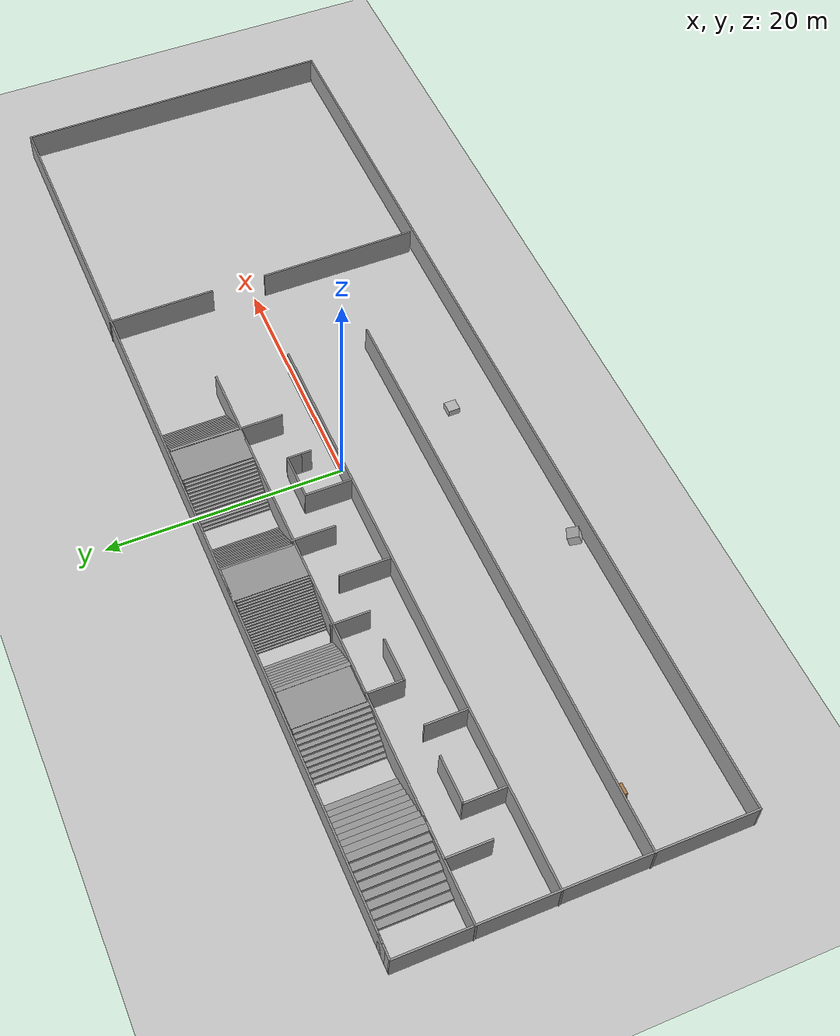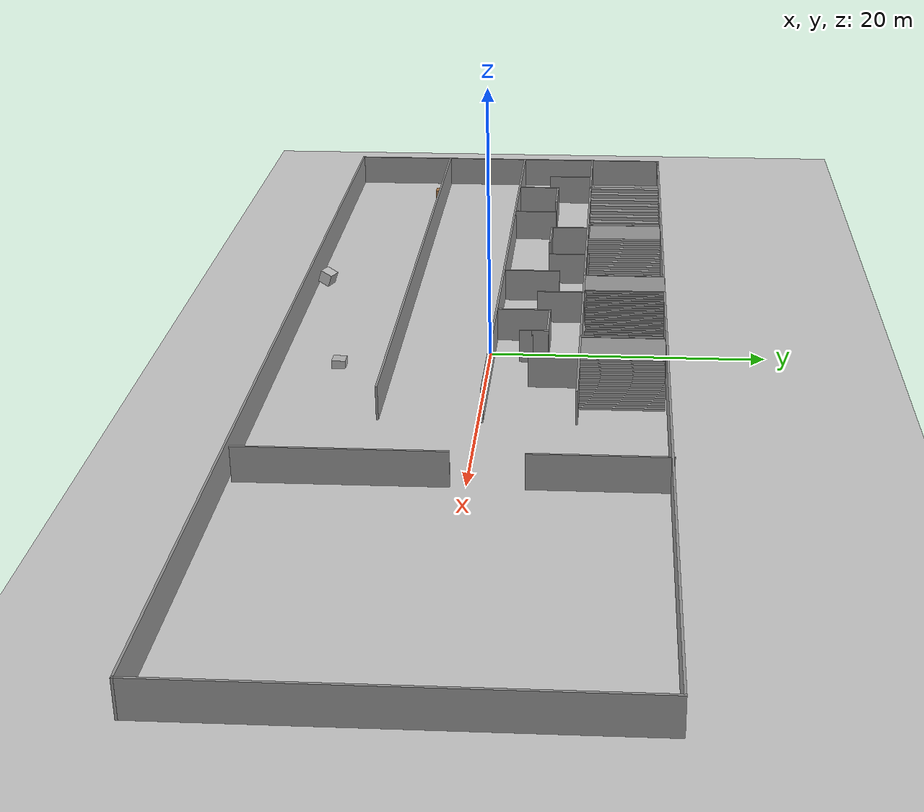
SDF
<sdf version="1.7">
 <world name="default">
  <light name="sun" type="directional">
   <pose>0 0 10 0 -0 0</pose>
   <diffuse>0.8 0.8 0.8 1</diffuse>
   <specular>0.2 0.2 0.2 1</specular>
   <attenuation>
    <range>1000</range>
    <constant>0.9</constant>
    <linear>0.01</linear>
    <quadratic>0.001</quadratic>
   </attenuation>
   <direction>-0.5 0.1 -0.9</direction>
   <spot><inner_angle>0</inner_angle><outer_angle>0</outer_angle><falloff>0</falloff></spot>
  </light>
  <model name="ground_plane">
   <static>1</static>
   <link name="link">
    <collision name="collision">
     <geometry><plane><normal>0 0 1</normal><size>100 100</size></plane></geometry>
     <surface>
      <contact><collide_bitmask>65535</collide_bitmask></contact>
      <friction><ode><mu>100</mu><mu2>50</mu2></ode></friction>
     </surface>
    </collision>
    <visual name="visual">
     <cast_shadows>0</cast_shadows>
     <geometry><plane><normal>0 0 1</normal><size>100 100</size></plane></geometry>
     <material>
      <script><uri>file://media/materials/scripts/gazebo.material</uri><name>Gazebo/Grey</name></script>
     </material>
    </visual>
   </link>
  </model>
  <gravity>0 0 -9.8</gravity>
  <magnetic_field>6e-06 2.3e-05 -4.2e-05</magnetic_field>
  <atmosphere type="adiabatic"/>
  <physics type="ode">
   <max_step_size>0.001</max_step_size>
   <real_time_factor>1</real_time_factor>
   <real_time_update_rate>1000</real_time_update_rate>
  </physics>
  <scene><ambient>0.4 0.4 0.4 1</ambient><background>0.7 0.7 0.7 1</background><shadows>1</shadows></scene>
  <audio><device>default</device></audio>
  <spherical_coordinates>
   <surface_model>EARTH_WGS84</surface_model>
   <latitude_deg>0</latitude_deg>
   <longitude_deg>0</longitude_deg>
   <elevation>0</elevation>
   <heading_deg>0</heading_deg>
  </spherical_coordinates>
  <model name="Parkour_0">
   <pose>2.61354 -1.10314 0 0 -0 0</pose>
   <link name="Stairs_0">
    <visual name="Stairs_0_Visual_0">
     <pose>6.1312 10.7342 0.083333 0 -0 -1.5708</pose>
     <geometry><box><size>5.922 0.233333 0.166667</size></box></geometry>
     <material>
      <script><uri>file://media/materials/scripts/gazebo.material</uri><name>Gazebo/Grey</name></script>
      <ambient>1 1 1 1</ambient>
     </material>
     <meta><layer>0</layer></meta>
    </visual>
    <collision name="Stairs_0_Collision_0">
     <geometry><box><size>5.922 0.233333 0.166667</size></box></geometry>
     <pose>6.1312 10.7342 0.083333 0 -0 -1.5708</pose>
    </collision>
    <visual name="Stairs_0_Visual_1">
     <pose>5.89787 10.7342 0.25 0 -0 -1.5708</pose>
     <geometry><box><size>5.922 0.233333 0.166667</size></box></geometry>
     <material>
      <script><uri>file://media/materials/scripts/gazebo.material</uri><name>Gazebo/Grey</name></script>
      <ambient>1 1 1 1</ambient>
     </material>
     <meta><layer>0</layer></meta>
    </visual>
    <collision name="Stairs_0_Collision_1">
     <geometry><box><size>5.922 0.233333 0.166667</size></box></geometry>
     <pose>5.89787 10.7342 0.25 0 -0 -1.5708</pose>
    </collision>
    <visual name="Stairs_0_Visual_2">
     <pose>5.66454 10.7342 0.416667 0 -0 -1.5708</pose>
     <geometry><box><size>5.922 0.233333 0.166667</size></box></geometry>
     <material>
      <script><uri>file://media/materials/scripts/gazebo.material</uri><name>Gazebo/Grey</name></script>
      <ambient>1 1 1 1</ambient>
     </material>
     <meta><layer>0</layer></meta>
    </visual>
    <collision name="Stairs_0_Collision_2">
     <geometry><box><size>5.922 0.233333 0.166667</size></box></geometry>
     <pose>5.66454 10.7342 0.416667 0 -0 -1.5708</pose>
    </collision>
    <visual name="Stairs_0_Visual_3">
     <pose>5.43121 10.7342 0.583333 0 -0 -1.5708</pose>
     <geometry><box><size>5.922 0.233333 0.166667</size></box></geometry>
     <material>
      <script><uri>file://media/materials/scripts/gazebo.material</uri><name>Gazebo/Grey</name></script>
      <ambient>1 1 1 1</ambient>
     </material>
     <meta><layer>0</layer></meta>
    </visual>
    <collision name="Stairs_0_Collision_3">
     <geometry><box><size>5.922 0.233333 0.166667</size></box></geometry>
     <pose>5.43121 10.7342 0.583333 0 -0 -1.5708</pose>
    </collision>
    <visual name="Stairs_0_Visual_4">
     <pose>5.19787 10.7342 0.75 0 -0 -1.5708</pose>
     <geometry><box><size>5.922 0.233333 0.166667</size></box></geometry>
     <material>
      <script><uri>file://media/materials/scripts/gazebo.material</uri><name>Gazebo/Grey</name></script>
      <ambient>1 1 1 1</ambient>
     </material>
     <meta><layer>0</layer></meta>
    </visual>
    <collision name="Stairs_0_Collision_4">
     <geometry><box><size>5.922 0.233333 0.166667</size></box></geometry>
     <pose>5.19787 10.7342 0.75 0 -0 -1.5708</pose>
    </collision>
    <visual name="Stairs_0_Visual_5">
     <pose>4.96454 10.7342 0.916667 0 -0 -1.5708</pose>
     <geometry><box><size>5.922 0.233333 0.166667</size></box></geometry>
     <material>
      <script><uri>file://media/materials/scripts/gazebo.material</uri><name>Gazebo/Grey</name></script>
      <ambient>1 1 1 1</ambient>
     </material>
     <meta><layer>0</layer></meta>
    </visual>
    <collision name="Stairs_0_Collision_5">
     <geometry><box><size>5.922 0.233333 0.166667</size></box></geometry>
     <pose>4.96454 10.7342 0.916667 0 -0 -1.5708</pose>
    </collision>
    <visual name="Stairs_0_Visual_6">
     <pose>4.73121 10.7342 1.08333 0 -0 -1.5708</pose>
     <geometry><box><size>5.922 0.233333 0.166667</size></box></geometry>
     <material>
      <script><uri>file://media/materials/scripts/gazebo.material</uri><name>Gazebo/Grey</name></script>
      <ambient>1 1 1 1</ambient>
     </material>
     <meta><layer>0</layer></meta>
    </visual>
    <collision name="Stairs_0_Collision_6">
     <geometry><box><size>5.922 0.233333 0.166667</size></box></geometry>
     <pose>4.73121 10.7342 1.08333 0 -0 -1.5708</pose>
    </collision>
    <visual name="Stairs_0_Visual_7">
     <pose>4.49787 10.7342 1.25 0 -0 -1.5708</pose>
     <geometry><box><size>5.922 0.233333 0.166667</size></box></geometry>
     <material>
      <script><uri>file://media/materials/scripts/gazebo.material</uri><name>Gazebo/Grey</name></script>
      <ambient>1 1 1 1</ambient>
     </material>
     <meta><layer>0</layer></meta>
    </visual>
    <collision name="Stairs_0_Collision_7">
     <geometry><box><size>5.922 0.233333 0.166667</size></box></geometry>
     <pose>4.49787 10.7342 1.25 0 -0 -1.5708</pose>
    </collision>
    <visual name="Stairs_0_Visual_8">
     <pose>4.26454 10.7342 1.41667 0 -0 -1.5708</pose>
     <geometry><box><size>5.922 0.233333 0.166667</size></box></geometry>
     <material>
      <script><uri>file://media/materials/scripts/gazebo.material</uri><name>Gazebo/Grey</name></script>
      <ambient>1 1 1 1</ambient>
     </material>
     <meta><layer>0</layer></meta>
    </visual>
    <collision name="Stairs_0_Collision_8">
     <geometry><box><size>5.922 0.233333 0.166667</size></box></geometry>
     <pose>4.26454 10.7342 1.41667 0 -0 -1.5708</pose>
    </collision>
    <visual name="Stairs_0_Visual_9">
     <pose>4.0312 10.7342 1.58333 0 -0 -1.5708</pose>
     <geometry><box><size>5.922 0.233333 0.166667</size></box></geometry>
     <material>
      <script><uri>file://media/materials/scripts/gazebo.material</uri><name>Gazebo/Grey</name></script>
      <ambient>1 1 1 1</ambient>
     </material>
     <meta><layer>0</layer></meta>
    </visual>
    <collision name="Stairs_0_Collision_9">
     <geometry><box><size>5.922 0.233333 0.166667</size></box></geometry>
     <pose>4.0312 10.7342 1.58333 0 -0 -1.5708</pose>
    </collision>
    <visual name="Stairs_0_Visual_10">
     <pose>3.79787 10.7342 1.75 0 -0 -1.5708</pose>
     <geometry><box><size>5.922 0.233333 0.166667</size></box></geometry>
     <material>
      <script><uri>file://media/materials/scripts/gazebo.material</uri><name>Gazebo/Grey</name></script>
      <ambient>1 1 1 1</ambient>
     </material>
     <meta><layer>0</layer></meta>
    </visual>
    <collision name="Stairs_0_Collision_10">
     <geometry><box><size>5.922 0.233333 0.166667</size></box></geometry>
     <pose>3.79787 10.7342 1.75 0 -0 -1.5708</pose>
    </collision>
    <visual name="Stairs_0_Visual_11">
     <pose>3.56454 10.7342 1.91667 0 -0 -1.5708</pose>
     <geometry><box><size>5.922 0.233333 0.166667</size></box></geometry>
     <material>
      <script><uri>file://media/materials/scripts/gazebo.material</uri><name>Gazebo/Grey</name></script>
      <ambient>1 1 1 1</ambient>
     </material>
     <meta><layer>0</layer></meta>
    </visual>
    <collision name="Stairs_0_Collision_11">
     <geometry><box><size>5.922 0.233333 0.166667</size></box></geometry>
     <pose>3.56454 10.7342 1.91667 0 -0 -1.5708</pose>
    </collision>
    <visual name="Stairs_0_Visual_12">
     <pose>3.3312 10.7342 2.08333 0 -0 -1.5708</pose>
     <geometry><box><size>5.922 0.233333 0.166667</size></box></geometry>
     <material>
      <script><uri>file://media/materials/scripts/gazebo.material</uri><name>Gazebo/Grey</name></script>
      <ambient>1 1 1 1</ambient>
     </material>
     <meta><layer>0</layer></meta>
    </visual>
    <collision name="Stairs_0_Collision_12">
     <geometry><box><size>5.922 0.233333 0.166667</size></box></geometry>
     <pose>3.3312 10.7342 2.08333 0 -0 -1.5708</pose>
    </collision>
    <visual name="Stairs_0_Visual_13">
     <pose>3.09787 10.7342 2.25 0 -0 -1.5708</pose>
     <geometry><box><size>5.922 0.233333 0.166667</size></box></geometry>
     <material>
      <script><uri>file://media/materials/scripts/gazebo.material</uri><name>Gazebo/Grey</name></script>
      <ambient>1 1 1 1</ambient>
     </material>
     <meta><layer>0</layer></meta>
    </visual>
    <collision name="Stairs_0_Collision_13">
     <geometry><box><size>5.922 0.233333 0.166667</size></box></geometry>
     <pose>3.09787 10.7342 2.25 0 -0 -1.5708</pose>
    </collision>
    <visual name="Stairs_0_Visual_14">
     <pose>2.86454 10.7342 2.41667 0 -0 -1.5708</pose>
     <geometry><box><size>5.922 0.233333 0.166667</size></box></geometry>
     <material>
      <script><uri>file://media/materials/scripts/gazebo.material</uri><name>Gazebo/Grey</name></script>
      <ambient>1 1 1 1</ambient>
     </material>
     <meta><layer>0</layer></meta>
    </visual>
    <collision name="Stairs_0_Collision_14">
     <geometry><box><size>5.922 0.233333 0.166667</size></box></geometry>
     <pose>2.86454 10.7342 2.41667 0 -0 -1.5708</pose>
    </collision>
   </link>
   <link name="Stairs_1">
    <visual name="Stairs_1_Visual_0">
     <pose>-3.78047 10.7035 0.083333 0 -0 1.5708</pose>
     <geometry><box><size>5.98376 0.233333 0.166667</size></box></geometry>
     <material>
      <script><uri>file://media/materials/scripts/gazebo.material</uri><name>Gazebo/Grey</name></script>
      <ambient>1 1 1 1</ambient>
     </material>
     <meta><layer>0</layer></meta>
    </visual>
    <collision name="Stairs_1_Collision_0">
     <geometry><box><size>5.98376 0.233333 0.166667</size></box></geometry>
     <pose>-3.78047 10.7035 0.083333 0 -0 1.5708</pose>
    </collision>
    <visual name="Stairs_1_Visual_1">
     <pose>-3.54714 10.7035 0.25 0 -0 1.5708</pose>
     <geometry><box><size>5.98376 0.233333 0.166667</size></box></geometry>
     <material>
      <script><uri>file://media/materials/scripts/gazebo.material</uri><name>Gazebo/Grey</name></script>
      <ambient>1 1 1 1</ambient>
     </material>
     <meta><layer>0</layer></meta>
    </visual>
    <collision name="Stairs_1_Collision_1">
     <geometry><box><size>5.98376 0.233333 0.166667</size></box></geometry>
     <pose>-3.54714 10.7035 0.25 0 -0 1.5708</pose>
    </collision>
    <visual name="Stairs_1_Visual_2">
     <pose>-3.31381 10.7035 0.416667 0 -0 1.5708</pose>
     <geometry><box><size>5.98376 0.233333 0.166667</size></box></geometry>
     <material>
      <script><uri>file://media/materials/scripts/gazebo.material</uri><name>Gazebo/Grey</name></script>
      <ambient>1 1 1 1</ambient>
     </material>
     <meta><layer>0</layer></meta>
    </visual>
    <collision name="Stairs_1_Collision_2">
     <geometry><box><size>5.98376 0.233333 0.166667</size></box></geometry>
     <pose>-3.31381 10.7035 0.416667 0 -0 1.5708</pose>
    </collision>
    <visual name="Stairs_1_Visual_3">
     <pose>-3.08047 10.7035 0.583333 0 -0 1.5708</pose>
     <geometry><box><size>5.98376 0.233333 0.166667</size></box></geometry>
     <material>
      <script><uri>file://media/materials/scripts/gazebo.material</uri><name>Gazebo/Grey</name></script>
      <ambient>1 1 1 1</ambient>
     </material>
     <meta><layer>0</layer></meta>
    </visual>
    <collision name="Stairs_1_Collision_3">
     <geometry><box><size>5.98376 0.233333 0.166667</size></box></geometry>
     <pose>-3.08047 10.7035 0.583333 0 -0 1.5708</pose>
    </collision>
    <visual name="Stairs_1_Visual_4">
     <pose>-2.84714 10.7035 0.75 0 -0 1.5708</pose>
     <geometry><box><size>5.98376 0.233333 0.166667</size></box></geometry>
     <material>
      <script><uri>file://media/materials/scripts/gazebo.material</uri><name>Gazebo/Grey</name></script>
      <ambient>1 1 1 1</ambient>
     </material>
     <meta><layer>0</layer></meta>
    </visual>
    <collision name="Stairs_1_Collision_4">
     <geometry><box><size>5.98376 0.233333 0.166667</size></box></geometry>
     <pose>-2.84714 10.7035 0.75 0 -0 1.5708</pose>
    </collision>
    <visual name="Stairs_1_Visual_5">
     <pose>-2.61381 10.7035 0.916667 0 -0 1.5708</pose>
     <geometry><box><size>5.98376 0.233333 0.166667</size></box></geometry>
     <material>
      <script><uri>file://media/materials/scripts/gazebo.material</uri><name>Gazebo/Grey</name></script>
      <ambient>1 1 1 1</ambient>
     </material>
     <meta><layer>0</layer></meta>
    </visual>
    <collision name="Stairs_1_Collision_5">
     <geometry><box><size>5.98376 0.233333 0.166667</size></box></geometry>
     <pose>-2.61381 10.7035 0.916667 0 -0 1.5708</pose>
    </collision>
    <visual name="Stairs_1_Visual_6">
     <pose>-2.38047 10.7035 1.08333 0 -0 1.5708</pose>
     <geometry><box><size>5.98376 0.233333 0.166667</size></box></geometry>
     <material>
      <script><uri>file://media/materials/scripts/gazebo.material</uri><name>Gazebo/Grey</name></script>
      <ambient>1 1 1 1</ambient>
     </material>
     <meta><layer>0</layer></meta>
    </visual>
    <collision name="Stairs_1_Collision_6">
     <geometry><box><size>5.98376 0.233333 0.166667</size></box></geometry>
     <pose>-2.38047 10.7035 1.08333 0 -0 1.5708</pose>
    </collision>
    <visual name="Stairs_1_Visual_7">
     <pose>-2.14714 10.7035 1.25 0 -0 1.5708</pose>
     <geometry><box><size>5.98376 0.233333 0.166667</size></box></geometry>
     <material>
      <script><uri>file://media/materials/scripts/gazebo.material</uri><name>Gazebo/Grey</name></script>
      <ambient>1 1 1 1</ambient>
     </material>
     <meta><layer>0</layer></meta>
    </visual>
    <collision name="Stairs_1_Collision_7">
     <geometry><box><size>5.98376 0.233333 0.166667</size></box></geometry>
     <pose>-2.14714 10.7035 1.25 0 -0 1.5708</pose>
    </collision>
    <visual name="Stairs_1_Visual_8">
     <pose>-1.91381 10.7035 1.41667 0 -0 1.5708</pose>
     <geometry><box><size>5.98376 0.233333 0.166667</size></box></geometry>
     <material>
      <script><uri>file://media/materials/scripts/gazebo.material</uri><name>Gazebo/Grey</name></script>
      <ambient>1 1 1 1</ambient>
     </material>
     <meta><layer>0</layer></meta>
    </visual>
    <collision name="Stairs_1_Collision_8">
     <geometry><box><size>5.98376 0.233333 0.166667</size></box></geometry>
     <pose>-1.91381 10.7035 1.41667 0 -0 1.5708</pose>
    </collision>
    <visual name="Stairs_1_Visual_9">
     <pose>-1.68047 10.7035 1.58333 0 -0 1.5708</pose>
     <geometry><box><size>5.98376 0.233333 0.166667</size></box></geometry>
     <material>
      <script><uri>file://media/materials/scripts/gazebo.material</uri><name>Gazebo/Grey</name></script>
      <ambient>1 1 1 1</ambient>
     </material>
     <meta><layer>0</layer></meta>
    </visual>
    <collision name="Stairs_1_Collision_9">
     <geometry><box><size>5.98376 0.233333 0.166667</size></box></geometry>
     <pose>-1.68047 10.7035 1.58333 0 -0 1.5708</pose>
    </collision>
    <visual name="Stairs_1_Visual_10">
     <pose>-1.44714 10.7035 1.75 0 -0 1.5708</pose>
     <geometry><box><size>5.98376 0.233333 0.166667</size></box></geometry>
     <material>
      <script><uri>file://media/materials/scripts/gazebo.material</uri><name>Gazebo/Grey</name></script>
      <ambient>1 1 1 1</ambient>
     </material>
     <meta><layer>0</layer></meta>
    </visual>
    <collision name="Stairs_1_Collision_10">
     <geometry><box><size>5.98376 0.233333 0.166667</size></box></geometry>
     <pose>-1.44714 10.7035 1.75 0 -0 1.5708</pose>
    </collision>
    <visual name="Stairs_1_Visual_11">
     <pose>-1.21381 10.7035 1.91667 0 -0 1.5708</pose>
     <geometry><box><size>5.98376 0.233333 0.166667</size></box></geometry>
     <material>
      <script><uri>file://media/materials/scripts/gazebo.material</uri><name>Gazebo/Grey</name></script>
      <ambient>1 1 1 1</ambient>
     </material>
     <meta><layer>0</layer></meta>
    </visual>
    <collision name="Stairs_1_Collision_11">
     <geometry><box><size>5.98376 0.233333 0.166667</size></box></geometry>
     <pose>-1.21381 10.7035 1.91667 0 -0 1.5708</pose>
    </collision>
    <visual name="Stairs_1_Visual_12">
     <pose>-0.980473 10.7035 2.08333 0 -0 1.5708</pose>
     <geometry><box><size>5.98376 0.233333 0.166667</size></box></geometry>
     <material>
      <script><uri>file://media/materials/scripts/gazebo.material</uri><name>Gazebo/Grey</name></script>
      <ambient>1 1 1 1</ambient>
     </material>
     <meta><layer>0</layer></meta>
    </visual>
    <collision name="Stairs_1_Collision_12">
     <geometry><box><size>5.98376 0.233333 0.166667</size></box></geometry>
     <pose>-0.980473 10.7035 2.08333 0 -0 1.5708</pose>
    </collision>
    <visual name="Stairs_1_Visual_13">
     <pose>-0.74714 10.7035 2.25 0 -0 1.5708</pose>
     <geometry><box><size>5.98376 0.233333 0.166667</size></box></geometry>
     <material>
      <script><uri>file://media/materials/scripts/gazebo.material</uri><name>Gazebo/Grey</name></script>
      <ambient>1 1 1 1</ambient>
     </material>
     <meta><layer>0</layer></meta>
    </visual>
    <collision name="Stairs_1_Collision_13">
     <geometry><box><size>5.98376 0.233333 0.166667</size></box></geometry>
     <pose>-0.74714 10.7035 2.25 0 -0 1.5708</pose>
    </collision>
    <visual name="Stairs_1_Visual_14">
     <pose>-0.513806 10.7035 2.41667 0 -0 1.5708</pose>
     <geometry><box><size>5.98376 0.233333 0.166667</size></box></geometry>
     <material>
      <script><uri>file://media/materials/scripts/gazebo.material</uri><name>Gazebo/Grey</name></script>
      <ambient>1 1 1 1</ambient>
     </material>
     <meta><layer>0</layer></meta>
    </visual>
    <collision name="Stairs_1_Collision_14">
     <geometry><box><size>5.98376 0.233333 0.166667</size></box></geometry>
     <pose>-0.513806 10.7035 2.41667 0 -0 1.5708</pose>
    </collision>
   </link>
   <link name="Stairs_2">
    <visual name="Stairs_2_Visual_0">
     <pose>-38.5274 10.758 0.15625 0 -0 1.5708</pose>
     <geometry><box><size>6.14 0.612955 0.3125</size></box></geometry>
     <material>
      <script><uri>file://media/materials/scripts/gazebo.material</uri><name>Gazebo/Grey</name></script>
      <ambient>1 1 1 1</ambient>
     </material>
     <meta><layer>0</layer></meta>
    </visual>
    <collision name="Stairs_2_Collision_0">
     <geometry><box><size>6.14 0.612955 0.3125</size></box></geometry>
     <pose>-38.5274 10.758 0.15625 0 -0 1.5708</pose>
    </collision>
    <visual name="Stairs_2_Visual_1">
     <pose>-37.9145 10.758 0.46875 0 -0 1.5708</pose>
     <geometry><box><size>6.14 0.612955 0.3125</size></box></geometry>
     <material>
      <script><uri>file://media/materials/scripts/gazebo.material</uri><name>Gazebo/Grey</name></script>
      <ambient>1 1 1 1</ambient>
     </material>
     <meta><layer>0</layer></meta>
    </visual>
    <collision name="Stairs_2_Collision_1">
     <geometry><box><size>6.14 0.612955 0.3125</size></box></geometry>
     <pose>-37.9145 10.758 0.46875 0 -0 1.5708</pose>
    </collision>
    <visual name="Stairs_2_Visual_2">
     <pose>-37.3015 10.758 0.78125 0 -0 1.5708</pose>
     <geometry><box><size>6.14 0.612955 0.3125</size></box></geometry>
     <material>
      <script><uri>file://media/materials/scripts/gazebo.material</uri><name>Gazebo/Grey</name></script>
      <ambient>1 1 1 1</ambient>
     </material>
     <meta><layer>0</layer></meta>
    </visual>
    <collision name="Stairs_2_Collision_2">
     <geometry><box><size>6.14 0.612955 0.3125</size></box></geometry>
     <pose>-37.3015 10.758 0.78125 0 -0 1.5708</pose>
    </collision>
    <visual name="Stairs_2_Visual_3">
     <pose>-36.6885 10.758 1.09375 0 -0 1.5708</pose>
     <geometry><box><size>6.14 0.612955 0.3125</size></box></geometry>
     <material>
      <script><uri>file://media/materials/scripts/gazebo.material</uri><name>Gazebo/Grey</name></script>
      <ambient>1 1 1 1</ambient>
     </material>
     <meta><layer>0</layer></meta>
    </visual>
    <collision name="Stairs_2_Collision_3">
     <geometry><box><size>6.14 0.612955 0.3125</size></box></geometry>
     <pose>-36.6885 10.758 1.09375 0 -0 1.5708</pose>
    </collision>
    <visual name="Stairs_2_Visual_4">
     <pose>-36.0756 10.758 1.40625 0 -0 1.5708</pose>
     <geometry><box><size>6.14 0.612955 0.3125</size></box></geometry>
     <material>
      <script><uri>file://media/materials/scripts/gazebo.material</uri><name>Gazebo/Grey</name></script>
      <ambient>1 1 1 1</ambient>
     </material>
     <meta><layer>0</layer></meta>
    </visual>
    <collision name="Stairs_2_Collision_4">
     <geometry><box><size>6.14 0.612955 0.3125</size></box></geometry>
     <pose>-36.0756 10.758 1.40625 0 -0 1.5708</pose>
    </collision>
    <visual name="Stairs_2_Visual_5">
     <pose>-35.4626 10.758 1.71875 0 -0 1.5708</pose>
     <geometry><box><size>6.14 0.612955 0.3125</size></box></geometry>
     <material>
      <script><uri>file://media/materials/scripts/gazebo.material</uri><name>Gazebo/Grey</name></script>
      <ambient>1 1 1 1</ambient>
     </material>
     <meta><layer>0</layer></meta>
    </visual>
    <collision name="Stairs_2_Collision_5">
     <geometry><box><size>6.14 0.612955 0.3125</size></box></geometry>
     <pose>-35.4626 10.758 1.71875 0 -0 1.5708</pose>
    </collision>
    <visual name="Stairs_2_Visual_6">
     <pose>-34.8497 10.758 2.03125 0 -0 1.5708</pose>
     <geometry><box><size>6.14 0.612955 0.3125</size></box></geometry>
     <material>
      <script><uri>file://media/materials/scripts/gazebo.material</uri><name>Gazebo/Grey</name></script>
      <ambient>1 1 1 1</ambient>
     </material>
     <meta><layer>0</layer></meta>
    </visual>
    <collision name="Stairs_2_Collision_6">
     <geometry><box><size>6.14 0.612955 0.3125</size></box></geometry>
     <pose>-34.8497 10.758 2.03125 0 -0 1.5708</pose>
    </collision>
    <visual name="Stairs_2_Visual_7">
     <pose>-34.2367 10.758 2.34375 0 -0 1.5708</pose>
     <geometry><box><size>6.14 0.612955 0.3125</size></box></geometry>
     <material>
      <script><uri>file://media/materials/scripts/gazebo.material</uri><name>Gazebo/Grey</name></script>
      <ambient>1 1 1 1</ambient>
     </material>
     <meta><layer>0</layer></meta>
    </visual>
    <collision name="Stairs_2_Collision_7">
     <geometry><box><size>6.14 0.612955 0.3125</size></box></geometry>
     <pose>-34.2367 10.758 2.34375 0 -0 1.5708</pose>
    </collision>
   </link>
   <link name="Stairs_3">
    <visual name="Stairs_3_Visual_0">
     <pose>-29.4585 10.758 0.15625 0 0 -1.5708</pose>
     <geometry><box><size>6.14 0.601258 0.3125</size></box></geometry>
     <material>
      <script><uri>file://media/materials/scripts/gazebo.material</uri><name>Gazebo/Grey</name></script>
      <ambient>1 1 1 1</ambient>
     </material>
     <meta><layer>0</layer></meta>
    </visual>
    <collision name="Stairs_3_Collision_0">
     <geometry><box><size>6.14 0.601258 0.3125</size></box></geometry>
     <pose>-29.4585 10.758 0.15625 0 0 -1.5708</pose>
    </collision>
    <visual name="Stairs_3_Visual_1">
     <pose>-30.0597 10.758 0.46875 0 0 -1.5708</pose>
     <geometry><box><size>6.14 0.601258 0.3125</size></box></geometry>
     <material>
      <script><uri>file://media/materials/scripts/gazebo.material</uri><name>Gazebo/Grey</name></script>
      <ambient>1 1 1 1</ambient>
     </material>
     <meta><layer>0</layer></meta>
    </visual>
    <collision name="Stairs_3_Collision_1">
     <geometry><box><size>6.14 0.601258 0.3125</size></box></geometry>
     <pose>-30.0597 10.758 0.46875 0 0 -1.5708</pose>
    </collision>
    <visual name="Stairs_3_Visual_2">
     <pose>-30.661 10.758 0.78125 0 0 -1.5708</pose>
     <geometry><box><size>6.14 0.601258 0.3125</size></box></geometry>
     <material>
      <script><uri>file://media/materials/scripts/gazebo.material</uri><name>Gazebo/Grey</name></script>
      <ambient>1 1 1 1</ambient>
     </material>
     <meta><layer>0</layer></meta>
    </visual>
    <collision name="Stairs_3_Collision_2">
     <geometry><box><size>6.14 0.601258 0.3125</size></box></geometry>
     <pose>-30.661 10.758 0.78125 0 0 -1.5708</pose>
    </collision>
    <visual name="Stairs_3_Visual_3">
     <pose>-31.2623 10.758 1.09375 0 0 -1.5708</pose>
     <geometry><box><size>6.14 0.601258 0.3125</size></box></geometry>
     <material>
      <script><uri>file://media/materials/scripts/gazebo.material</uri><name>Gazebo/Grey</name></script>
      <ambient>1 1 1 1</ambient>
     </material>
     <meta><layer>0</layer></meta>
    </visual>
    <collision name="Stairs_3_Collision_3">
     <geometry><box><size>6.14 0.601258 0.3125</size></box></geometry>
     <pose>-31.2623 10.758 1.09375 0 0 -1.5708</pose>
    </collision>
    <visual name="Stairs_3_Visual_4">
     <pose>-31.8635 10.758 1.40625 0 0 -1.5708</pose>
     <geometry><box><size>6.14 0.601258 0.3125</size></box></geometry>
     <material>
      <script><uri>file://media/materials/scripts/gazebo.material</uri><name>Gazebo/Grey</name></script>
      <ambient>1 1 1 1</ambient>
     </material>
     <meta><layer>0</layer></meta>
    </visual>
    <collision name="Stairs_3_Collision_4">
     <geometry><box><size>6.14 0.601258 0.3125</size></box></geometry>
     <pose>-31.8635 10.758 1.40625 0 0 -1.5708</pose>
    </collision>
    <visual name="Stairs_3_Visual_5">
     <pose>-32.4648 10.758 1.71875 0 0 -1.5708</pose>
     <geometry><box><size>6.14 0.601258 0.3125</size></box></geometry>
     <material>
      <script><uri>file://media/materials/scripts/gazebo.material</uri><name>Gazebo/Grey</name></script>
      <ambient>1 1 1 1</ambient>
     </material>
     <meta><layer>0</layer></meta>
    </visual>
    <collision name="Stairs_3_Collision_5">
     <geometry><box><size>6.14 0.601258 0.3125</size></box></geometry>
     <pose>-32.4648 10.758 1.71875 0 0 -1.5708</pose>
    </collision>
    <visual name="Stairs_3_Visual_6">
     <pose>-33.066 10.758 2.03125 0 0 -1.5708</pose>
     <geometry><box><size>6.14 0.601258 0.3125</size></box></geometry>
     <material>
      <script><uri>file://media/materials/scripts/gazebo.material</uri><name>Gazebo/Grey</name></script>
      <ambient>1 1 1 1</ambient>
     </material>
     <meta><layer>0</layer></meta>
    </visual>
    <collision name="Stairs_3_Collision_6">
     <geometry><box><size>6.14 0.601258 0.3125</size></box></geometry>
     <pose>-33.066 10.758 2.03125 0 0 -1.5708</pose>
    </collision>
    <visual name="Stairs_3_Visual_7">
     <pose>-33.6673 10.758 2.34375 0 0 -1.5708</pose>
     <geometry><box><size>6.14 0.601258 0.3125</size></box></geometry>
     <material>
      <script><uri>file://media/materials/scripts/gazebo.material</uri><name>Gazebo/Grey</name></script>
      <ambient>1 1 1 1</ambient>
     </material>
     <meta><layer>0</layer></meta>
    </visual>
    <collision name="Stairs_3_Collision_7">
     <geometry><box><size>6.14 0.601258 0.3125</size></box></geometry>
     <pose>-33.6673 10.758 2.34375 0 0 -1.5708</pose>
    </collision>
   </link>
   <link name="Stairs_4">
    <visual name="Stairs_4_Visual_0">
     <pose>1.19165 10.744 1.25 0 -0 0</pose>
     <geometry><box><size>3 6.05994 2.5</size></box></geometry>
     <material>
      <script><uri>file://media/materials/scripts/gazebo.material</uri><name>Gazebo/Grey</name></script>
      <ambient>1 1 1 1</ambient>
     </material>
     <meta><layer>0</layer></meta>
    </visual>
    <collision name="Stairs_4_Collision_0">
     <geometry><box><size>3 6.05994 2.5</size></box></geometry>
     <pose>1.19165 10.744 1.25 0 -0 0</pose>
    </collision>
   </link>
   <link name="Stairs_21">
    <visual name="Stairs_21_Visual_0">
     <pose>-10.7697 10.8664 1.25 0 -0 0</pose>
     <geometry><box><size>3 6.141 2.5</size></box></geometry>
     <material>
      <script><uri>file://media/materials/scripts/gazebo.material</uri><name>Gazebo/Grey</name></script>
      <ambient>1 1 1 1</ambient>
     </material>
     <meta><layer>0</layer></meta>
    </visual>
    <collision name="Stairs_21_Collision_0">
     <geometry><box><size>3 6.141 2.5</size></box></geometry>
     <pose>-10.7697 10.8664 1.25 0 -0 0</pose>
    </collision>
   </link>
   <link name="Stairs_22">
    <visual name="Stairs_22_Visual_0">
     <pose>-22.2123 10.8352 1.25 0 -0 0</pose>
     <geometry><box><size>3.154 5.86 2.5</size></box></geometry>
     <material>
      <script><uri>file://media/materials/scripts/gazebo.material</uri><name>Gazebo/Grey</name></script>
      <ambient>1 1 1 1</ambient>
     </material>
     <meta><layer>0</layer></meta>
    </visual>
    <collision name="Stairs_22_Collision_0">
     <geometry><box><size>3.154 5.86 2.5</size></box></geometry>
     <pose>-22.2123 10.8352 1.25 0 -0 0</pose>
    </collision>
   </link>
   <link name="Stair_fix_later">
    <visual name="Stair_fix_later_Visual_0">
     <pose>-5.89199 10.8984 0.0625 0 0 -1.5708</pose>
     <geometry><box><size>6 0.175 0.125</size></box></geometry>
     <material>
      <script><uri>file://media/materials/scripts/gazebo.material</uri><name>Gazebo/Grey</name></script>
      <ambient>1 1 1 1</ambient>
     </material>
     <meta><layer>0</layer></meta>
    </visual>
    <collision name="Stair_fix_later_Collision_0">
     <geometry><box><size>6 0.175 0.125</size></box></geometry>
     <pose>-5.89199 10.8984 0.0625 0 0 -1.5708</pose>
    </collision>
    <visual name="Stair_fix_later_Visual_1">
     <pose>-6.06699 10.8984 0.1875 0 0 -1.5708</pose>
     <geometry><box><size>6 0.175 0.125</size></box></geometry>
     <material>
      <script><uri>file://media/materials/scripts/gazebo.material</uri><name>Gazebo/Grey</name></script>
      <ambient>1 1 1 1</ambient>
     </material>
     <meta><layer>0</layer></meta>
    </visual>
    <collision name="Stair_fix_later_Collision_1">
     <geometry><box><size>6 0.175 0.125</size></box></geometry>
     <pose>-6.06699 10.8984 0.1875 0 0 -1.5708</pose>
    </collision>
    <visual name="Stair_fix_later_Visual_2">
     <pose>-6.24199 10.8984 0.3125 0 0 -1.5708</pose>
     <geometry><box><size>6 0.175 0.125</size></box></geometry>
     <material>
      <script><uri>file://media/materials/scripts/gazebo.material</uri><name>Gazebo/Grey</name></script>
      <ambient>1 1 1 1</ambient>
     </material>
     <meta><layer>0</layer></meta>
    </visual>
    <collision name="Stair_fix_later_Collision_2">
     <geometry><box><size>6 0.175 0.125</size></box></geometry>
     <pose>-6.24199 10.8984 0.3125 0 0 -1.5708</pose>
    </collision>
    <visual name="Stair_fix_later_Visual_3">
     <pose>-6.41699 10.8984 0.4375 0 0 -1.5708</pose>
     <geometry><box><size>6 0.175 0.125</size></box></geometry>
     <material>
      <script><uri>file://media/materials/scripts/gazebo.material</uri><name>Gazebo/Grey</name></script>
      <ambient>1 1 1 1</ambient>
     </material>
     <meta><layer>0</layer></meta>
    </visual>
    <collision name="Stair_fix_later_Collision_3">
     <geometry><box><size>6 0.175 0.125</size></box></geometry>
     <pose>-6.41699 10.8984 0.4375 0 0 -1.5708</pose>
    </collision>
    <visual name="Stair_fix_later_Visual_4">
     <pose>-6.59199 10.8984 0.5625 0 0 -1.5708</pose>
     <geometry><box><size>6 0.175 0.125</size></box></geometry>
     <material>
      <script><uri>file://media/materials/scripts/gazebo.material</uri><name>Gazebo/Grey</name></script>
      <ambient>1 1 1 1</ambient>
     </material>
     <meta><layer>0</layer></meta>
    </visual>
    <collision name="Stair_fix_later_Collision_4">
     <geometry><box><size>6 0.175 0.125</size></box></geometry>
     <pose>-6.59199 10.8984 0.5625 0 0 -1.5708</pose>
    </collision>
    <visual name="Stair_fix_later_Visual_5">
     <pose>-6.76699 10.8984 0.6875 0 0 -1.5708</pose>
     <geometry><box><size>6 0.175 0.125</size></box></geometry>
     <material>
      <script><uri>file://media/materials/scripts/gazebo.material</uri><name>Gazebo/Grey</name></script>
      <ambient>1 1 1 1</ambient>
     </material>
     <meta><layer>0</layer></meta>
    </visual>
    <collision name="Stair_fix_later_Collision_5">
     <geometry><box><size>6 0.175 0.125</size></box></geometry>
     <pose>-6.76699 10.8984 0.6875 0 0 -1.5708</pose>
    </collision>
    <visual name="Stair_fix_later_Visual_6">
     <pose>-6.94199 10.8984 0.8125 0 0 -1.5708</pose>
     <geometry><box><size>6 0.175 0.125</size></box></geometry>
     <material>
      <script><uri>file://media/materials/scripts/gazebo.material</uri><name>Gazebo/Grey</name></script>
      <ambient>1 1 1 1</ambient>
     </material>
     <meta><layer>0</layer></meta>
    </visual>
    <collision name="Stair_fix_later_Collision_6">
     <geometry><box><size>6 0.175 0.125</size></box></geometry>
     <pose>-6.94199 10.8984 0.8125 0 0 -1.5708</pose>
    </collision>
    <visual name="Stair_fix_later_Visual_7">
     <pose>-7.11699 10.8984 0.9375 0 0 -1.5708</pose>
     <geometry><box><size>6 0.175 0.125</size></box></geometry>
     <material>
      <script><uri>file://media/materials/scripts/gazebo.material</uri><name>Gazebo/Grey</name></script>
      <ambient>1 1 1 1</ambient>
     </material>
     <meta><layer>0</layer></meta>
    </visual>
    <collision name="Stair_fix_later_Collision_7">
     <geometry><box><size>6 0.175 0.125</size></box></geometry>
     <pose>-7.11699 10.8984 0.9375 0 0 -1.5708</pose>
    </collision>
    <visual name="Stair_fix_later_Visual_8">
     <pose>-7.29199 10.8984 1.0625 0 0 -1.5708</pose>
     <geometry><box><size>6 0.175 0.125</size></box></geometry>
     <material>
      <script><uri>file://media/materials/scripts/gazebo.material</uri><name>Gazebo/Grey</name></script>
      <ambient>1 1 1 1</ambient>
     </material>
     <meta><layer>0</layer></meta>
    </visual>
    <collision name="Stair_fix_later_Collision_8">
     <geometry><box><size>6 0.175 0.125</size></box></geometry>
     <pose>-7.29199 10.8984 1.0625 0 0 -1.5708</pose>
    </collision>
    <visual name="Stair_fix_later_Visual_9">
     <pose>-7.46699 10.8984 1.1875 0 0 -1.5708</pose>
     <geometry><box><size>6 0.175 0.125</size></box></geometry>
     <material>
      <script><uri>file://media/materials/scripts/gazebo.material</uri><name>Gazebo/Grey</name></script>
      <ambient>1 1 1 1</ambient>
     </material>
     <meta><layer>0</layer></meta>
    </visual>
    <collision name="Stair_fix_later_Collision_9">
     <geometry><box><size>6 0.175 0.125</size></box></geometry>
     <pose>-7.46699 10.8984 1.1875 0 0 -1.5708</pose>
    </collision>
    <visual name="Stair_fix_later_Visual_10">
     <pose>-7.64199 10.8984 1.3125 0 0 -1.5708</pose>
     <geometry><box><size>6 0.175 0.125</size></box></geometry>
     <material>
      <script><uri>file://media/materials/scripts/gazebo.material</uri><name>Gazebo/Grey</name></script>
      <ambient>1 1 1 1</ambient>
     </material>
     <meta><layer>0</layer></meta>
    </visual>
    <collision name="Stair_fix_later_Collision_10">
     <geometry><box><size>6 0.175 0.125</size></box></geometry>
     <pose>-7.64199 10.8984 1.3125 0 0 -1.5708</pose>
    </collision>
    <visual name="Stair_fix_later_Visual_11">
     <pose>-7.81699 10.8984 1.4375 0 0 -1.5708</pose>
     <geometry><box><size>6 0.175 0.125</size></box></geometry>
     <material>
      <script><uri>file://media/materials/scripts/gazebo.material</uri><name>Gazebo/Grey</name></script>
      <ambient>1 1 1 1</ambient>
     </material>
     <meta><layer>0</layer></meta>
    </visual>
    <collision name="Stair_fix_later_Collision_11">
     <geometry><box><size>6 0.175 0.125</size></box></geometry>
     <pose>-7.81699 10.8984 1.4375 0 0 -1.5708</pose>
    </collision>
    <visual name="Stair_fix_later_Visual_12">
     <pose>-7.99199 10.8984 1.5625 0 0 -1.5708</pose>
     <geometry><box><size>6 0.175 0.125</size></box></geometry>
     <material>
      <script><uri>file://media/materials/scripts/gazebo.material</uri><name>Gazebo/Grey</name></script>
      <ambient>1 1 1 1</ambient>
     </material>
     <meta><layer>0</layer></meta>
    </visual>
    <collision name="Stair_fix_later_Collision_12">
     <geometry><box><size>6 0.175 0.125</size></box></geometry>
     <pose>-7.99199 10.8984 1.5625 0 0 -1.5708</pose>
    </collision>
    <visual name="Stair_fix_later_Visual_13">
     <pose>-8.16699 10.8984 1.6875 0 0 -1.5708</pose>
     <geometry><box><size>6 0.175 0.125</size></box></geometry>
     <material>
      <script><uri>file://media/materials/scripts/gazebo.material</uri><name>Gazebo/Grey</name></script>
      <ambient>1 1 1 1</ambient>
     </material>
     <meta><layer>0</layer></meta>
    </visual>
    <collision name="Stair_fix_later_Collision_13">
     <geometry><box><size>6 0.175 0.125</size></box></geometry>
     <pose>-8.16699 10.8984 1.6875 0 0 -1.5708</pose>
    </collision>
    <visual name="Stair_fix_later_Visual_14">
     <pose>-8.34199 10.8984 1.8125 0 0 -1.5708</pose>
     <geometry><box><size>6 0.175 0.125</size></box></geometry>
     <material>
      <script><uri>file://media/materials/scripts/gazebo.material</uri><name>Gazebo/Grey</name></script>
      <ambient>1 1 1 1</ambient>
     </material>
     <meta><layer>0</layer></meta>
    </visual>
    <collision name="Stair_fix_later_Collision_14">
     <geometry><box><size>6 0.175 0.125</size></box></geometry>
     <pose>-8.34199 10.8984 1.8125 0 0 -1.5708</pose>
    </collision>
    <visual name="Stair_fix_later_Visual_15">
     <pose>-8.51699 10.8984 1.9375 0 0 -1.5708</pose>
     <geometry><box><size>6 0.175 0.125</size></box></geometry>
     <material>
      <script><uri>file://media/materials/scripts/gazebo.material</uri><name>Gazebo/Grey</name></script>
      <ambient>1 1 1 1</ambient>
     </material>
     <meta><layer>0</layer></meta>
    </visual>
    <collision name="Stair_fix_later_Collision_15">
     <geometry><box><size>6 0.175 0.125</size></box></geometry>
     <pose>-8.51699 10.8984 1.9375 0 0 -1.5708</pose>
    </collision>
    <visual name="Stair_fix_later_Visual_16">
     <pose>-8.69199 10.8984 2.0625 0 0 -1.5708</pose>
     <geometry><box><size>6 0.175 0.125</size></box></geometry>
     <material>
      <script><uri>file://media/materials/scripts/gazebo.material</uri><name>Gazebo/Grey</name></script>
      <ambient>1 1 1 1</ambient>
     </material>
     <meta><layer>0</layer></meta>
    </visual>
    <collision name="Stair_fix_later_Collision_16">
     <geometry><box><size>6 0.175 0.125</size></box></geometry>
     <pose>-8.69199 10.8984 2.0625 0 0 -1.5708</pose>
    </collision>
    <visual name="Stair_fix_later_Visual_17">
     <pose>-8.86699 10.8984 2.1875 0 0 -1.5708</pose>
     <geometry><box><size>6 0.175 0.125</size></box></geometry>
     <material>
      <script><uri>file://media/materials/scripts/gazebo.material</uri><name>Gazebo/Grey</name></script>
      <ambient>1 1 1 1</ambient>
     </material>
     <meta><layer>0</layer></meta>
    </visual>
    <collision name="Stair_fix_later_Collision_17">
     <geometry><box><size>6 0.175 0.125</size></box></geometry>
     <pose>-8.86699 10.8984 2.1875 0 0 -1.5708</pose>
    </collision>
    <visual name="Stair_fix_later_Visual_18">
     <pose>-9.04199 10.8984 2.3125 0 0 -1.5708</pose>
     <geometry><box><size>6 0.175 0.125</size></box></geometry>
     <material>
      <script><uri>file://media/materials/scripts/gazebo.material</uri><name>Gazebo/Grey</name></script>
      <ambient>1 1 1 1</ambient>
     </material>
     <meta><layer>0</layer></meta>
    </visual>
    <collision name="Stair_fix_later_Collision_18">
     <geometry><box><size>6 0.175 0.125</size></box></geometry>
     <pose>-9.04199 10.8984 2.3125 0 0 -1.5708</pose>
    </collision>
    <visual name="Stair_fix_later_Visual_19">
     <pose>-9.21699 10.8984 2.4375 0 0 -1.5708</pose>
     <geometry><box><size>6 0.175 0.125</size></box></geometry>
     <material>
      <script><uri>file://media/materials/scripts/gazebo.material</uri><name>Gazebo/Grey</name></script>
      <ambient>1 1 1 1</ambient>
     </material>
     <meta><layer>0</layer></meta>
    </visual>
    <collision name="Stair_fix_later_Collision_19">
     <geometry><box><size>6 0.175 0.125</size></box></geometry>
     <pose>-9.21699 10.8984 2.4375 0 0 -1.5708</pose>
    </collision>
   </link>
   <link name="Stairs_5">
    <visual name="Stairs_5_Visual_0">
     <pose>-15.7266 10.7113 0.0625 0 -0 1.5708</pose>
     <geometry><box><size>6 0.175 0.125</size></box></geometry>
     <material>
      <script><uri>file://media/materials/scripts/gazebo.material</uri><name>Gazebo/Grey</name></script>
      <ambient>1 1 1 1</ambient>
     </material>
     <meta><layer>0</layer></meta>
    </visual>
    <collision name="Stairs_5_Collision_0">
     <geometry><box><size>6 0.175 0.125</size></box></geometry>
     <pose>-15.7266 10.7113 0.0625 0 -0 1.5708</pose>
    </collision>
    <visual name="Stairs_5_Visual_1">
     <pose>-15.5516 10.7113 0.1875 0 -0 1.5708</pose>
     <geometry><box><size>6 0.175 0.125</size></box></geometry>
     <material>
      <script><uri>file://media/materials/scripts/gazebo.material</uri><name>Gazebo/Grey</name></script>
      <ambient>1 1 1 1</ambient>
     </material>
     <meta><layer>0</layer></meta>
    </visual>
    <collision name="Stairs_5_Collision_1">
     <geometry><box><size>6 0.175 0.125</size></box></geometry>
     <pose>-15.5516 10.7113 0.1875 0 -0 1.5708</pose>
    </collision>
    <visual name="Stairs_5_Visual_2">
     <pose>-15.3766 10.7113 0.3125 0 -0 1.5708</pose>
     <geometry><box><size>6 0.175 0.125</size></box></geometry>
     <material>
      <script><uri>file://media/materials/scripts/gazebo.material</uri><name>Gazebo/Grey</name></script>
      <ambient>1 1 1 1</ambient>
     </material>
     <meta><layer>0</layer></meta>
    </visual>
    <collision name="Stairs_5_Collision_2">
     <geometry><box><size>6 0.175 0.125</size></box></geometry>
     <pose>-15.3766 10.7113 0.3125 0 -0 1.5708</pose>
    </collision>
    <visual name="Stairs_5_Visual_3">
     <pose>-15.2016 10.7113 0.4375 0 -0 1.5708</pose>
     <geometry><box><size>6 0.175 0.125</size></box></geometry>
     <material>
      <script><uri>file://media/materials/scripts/gazebo.material</uri><name>Gazebo/Grey</name></script>
      <ambient>1 1 1 1</ambient>
     </material>
     <meta><layer>0</layer></meta>
    </visual>
    <collision name="Stairs_5_Collision_3">
     <geometry><box><size>6 0.175 0.125</size></box></geometry>
     <pose>-15.2016 10.7113 0.4375 0 -0 1.5708</pose>
    </collision>
    <visual name="Stairs_5_Visual_4">
     <pose>-15.0266 10.7113 0.5625 0 -0 1.5708</pose>
     <geometry><box><size>6 0.175 0.125</size></box></geometry>
     <material>
      <script><uri>file://media/materials/scripts/gazebo.material</uri><name>Gazebo/Grey</name></script>
      <ambient>1 1 1 1</ambient>
     </material>
     <meta><layer>0</layer></meta>
    </visual>
    <collision name="Stairs_5_Collision_4">
     <geometry><box><size>6 0.175 0.125</size></box></geometry>
     <pose>-15.0266 10.7113 0.5625 0 -0 1.5708</pose>
    </collision>
    <visual name="Stairs_5_Visual_5">
     <pose>-14.8516 10.7113 0.6875 0 -0 1.5708</pose>
     <geometry><box><size>6 0.175 0.125</size></box></geometry>
     <material>
      <script><uri>file://media/materials/scripts/gazebo.material</uri><name>Gazebo/Grey</name></script>
      <ambient>1 1 1 1</ambient>
     </material>
     <meta><layer>0</layer></meta>
    </visual>
    <collision name="Stairs_5_Collision_5">
     <geometry><box><size>6 0.175 0.125</size></box></geometry>
     <pose>-14.8516 10.7113 0.6875 0 -0 1.5708</pose>
    </collision>
    <visual name="Stairs_5_Visual_6">
     <pose>-14.6766 10.7113 0.8125 0 -0 1.5708</pose>
     <geometry><box><size>6 0.175 0.125</size></box></geometry>
     <material>
      <script><uri>file://media/materials/scripts/gazebo.material</uri><name>Gazebo/Grey</name></script>
      <ambient>1 1 1 1</ambient>
     </material>
     <meta><layer>0</layer></meta>
    </visual>
    <collision name="Stairs_5_Collision_6">
     <geometry><box><size>6 0.175 0.125</size></box></geometry>
     <pose>-14.6766 10.7113 0.8125 0 -0 1.5708</pose>
    </collision>
    <visual name="Stairs_5_Visual_7">
     <pose>-14.5016 10.7113 0.9375 0 -0 1.5708</pose>
     <geometry><box><size>6 0.175 0.125</size></box></geometry>
     <material>
      <script><uri>file://media/materials/scripts/gazebo.material</uri><name>Gazebo/Grey</name></script>
      <ambient>1 1 1 1</ambient>
     </material>
     <meta><layer>0</layer></meta>
    </visual>
    <collision name="Stairs_5_Collision_7">
     <geometry><box><size>6 0.175 0.125</size></box></geometry>
     <pose>-14.5016 10.7113 0.9375 0 -0 1.5708</pose>
    </collision>
    <visual name="Stairs_5_Visual_8">
     <pose>-14.3266 10.7113 1.0625 0 -0 1.5708</pose>
     <geometry><box><size>6 0.175 0.125</size></box></geometry>
     <material>
      <script><uri>file://media/materials/scripts/gazebo.material</uri><name>Gazebo/Grey</name></script>
      <ambient>1 1 1 1</ambient>
     </material>
     <meta><layer>0</layer></meta>
    </visual>
    <collision name="Stairs_5_Collision_8">
     <geometry><box><size>6 0.175 0.125</size></box></geometry>
     <pose>-14.3266 10.7113 1.0625 0 -0 1.5708</pose>
    </collision>
    <visual name="Stairs_5_Visual_9">
     <pose>-14.1516 10.7113 1.1875 0 -0 1.5708</pose>
     <geometry><box><size>6 0.175 0.125</size></box></geometry>
     <material>
      <script><uri>file://media/materials/scripts/gazebo.material</uri><name>Gazebo/Grey</name></script>
      <ambient>1 1 1 1</ambient>
     </material>
     <meta><layer>0</layer></meta>
    </visual>
    <collision name="Stairs_5_Collision_9">
     <geometry><box><size>6 0.175 0.125</size></box></geometry>
     <pose>-14.1516 10.7113 1.1875 0 -0 1.5708</pose>
    </collision>
    <visual name="Stairs_5_Visual_10">
     <pose>-13.9766 10.7113 1.3125 0 -0 1.5708</pose>
     <geometry><box><size>6 0.175 0.125</size></box></geometry>
     <material>
      <script><uri>file://media/materials/scripts/gazebo.material</uri><name>Gazebo/Grey</name></script>
      <ambient>1 1 1 1</ambient>
     </material>
     <meta><layer>0</layer></meta>
    </visual>
    <collision name="Stairs_5_Collision_10">
     <geometry><box><size>6 0.175 0.125</size></box></geometry>
     <pose>-13.9766 10.7113 1.3125 0 -0 1.5708</pose>
    </collision>
    <visual name="Stairs_5_Visual_11">
     <pose>-13.8016 10.7113 1.4375 0 -0 1.5708</pose>
     <geometry><box><size>6 0.175 0.125</size></box></geometry>
     <material>
      <script><uri>file://media/materials/scripts/gazebo.material</uri><name>Gazebo/Grey</name></script>
      <ambient>1 1 1 1</ambient>
     </material>
     <meta><layer>0</layer></meta>
    </visual>
    <collision name="Stairs_5_Collision_11">
     <geometry><box><size>6 0.175 0.125</size></box></geometry>
     <pose>-13.8016 10.7113 1.4375 0 -0 1.5708</pose>
    </collision>
    <visual name="Stairs_5_Visual_12">
     <pose>-13.6266 10.7113 1.5625 0 -0 1.5708</pose>
     <geometry><box><size>6 0.175 0.125</size></box></geometry>
     <material>
      <script><uri>file://media/materials/scripts/gazebo.material</uri><name>Gazebo/Grey</name></script>
      <ambient>1 1 1 1</ambient>
     </material>
     <meta><layer>0</layer></meta>
    </visual>
    <collision name="Stairs_5_Collision_12">
     <geometry><box><size>6 0.175 0.125</size></box></geometry>
     <pose>-13.6266 10.7113 1.5625 0 -0 1.5708</pose>
    </collision>
    <visual name="Stairs_5_Visual_13">
     <pose>-13.4516 10.7113 1.6875 0 -0 1.5708</pose>
     <geometry><box><size>6 0.175 0.125</size></box></geometry>
     <material>
      <script><uri>file://media/materials/scripts/gazebo.material</uri><name>Gazebo/Grey</name></script>
      <ambient>1 1 1 1</ambient>
     </material>
     <meta><layer>0</layer></meta>
    </visual>
    <collision name="Stairs_5_Collision_13">
     <geometry><box><size>6 0.175 0.125</size></box></geometry>
     <pose>-13.4516 10.7113 1.6875 0 -0 1.5708</pose>
    </collision>
    <visual name="Stairs_5_Visual_14">
     <pose>-13.2766 10.7113 1.8125 0 -0 1.5708</pose>
     <geometry><box><size>6 0.175 0.125</size></box></geometry>
     <material>
      <script><uri>file://media/materials/scripts/gazebo.material</uri><name>Gazebo/Grey</name></script>
      <ambient>1 1 1 1</ambient>
     </material>
     <meta><layer>0</layer></meta>
    </visual>
    <collision name="Stairs_5_Collision_14">
     <geometry><box><size>6 0.175 0.125</size></box></geometry>
     <pose>-13.2766 10.7113 1.8125 0 -0 1.5708</pose>
    </collision>
    <visual name="Stairs_5_Visual_15">
     <pose>-13.1016 10.7113 1.9375 0 -0 1.5708</pose>
     <geometry><box><size>6 0.175 0.125</size></box></geometry>
     <material>
      <script><uri>file://media/materials/scripts/gazebo.material</uri><name>Gazebo/Grey</name></script>
      <ambient>1 1 1 1</ambient>
     </material>
     <meta><layer>0</layer></meta>
    </visual>
    <collision name="Stairs_5_Collision_15">
     <geometry><box><size>6 0.175 0.125</size></box></geometry>
     <pose>-13.1016 10.7113 1.9375 0 -0 1.5708</pose>
    </collision>
    <visual name="Stairs_5_Visual_16">
     <pose>-12.9266 10.7113 2.0625 0 -0 1.5708</pose>
     <geometry><box><size>6 0.175 0.125</size></box></geometry>
     <material>
      <script><uri>file://media/materials/scripts/gazebo.material</uri><name>Gazebo/Grey</name></script>
      <ambient>1 1 1 1</ambient>
     </material>
     <meta><layer>0</layer></meta>
    </visual>
    <collision name="Stairs_5_Collision_16">
     <geometry><box><size>6 0.175 0.125</size></box></geometry>
     <pose>-12.9266 10.7113 2.0625 0 -0 1.5708</pose>
    </collision>
    <visual name="Stairs_5_Visual_17">
     <pose>-12.7516 10.7113 2.1875 0 -0 1.5708</pose>
     <geometry><box><size>6 0.175 0.125</size></box></geometry>
     <material>
      <script><uri>file://media/materials/scripts/gazebo.material</uri><name>Gazebo/Grey</name></script>
      <ambient>1 1 1 1</ambient>
     </material>
     <meta><layer>0</layer></meta>
    </visual>
    <collision name="Stairs_5_Collision_17">
     <geometry><box><size>6 0.175 0.125</size></box></geometry>
     <pose>-12.7516 10.7113 2.1875 0 -0 1.5708</pose>
    </collision>
    <visual name="Stairs_5_Visual_18">
     <pose>-12.5766 10.7113 2.3125 0 -0 1.5708</pose>
     <geometry><box><size>6 0.175 0.125</size></box></geometry>
     <material>
      <script><uri>file://media/materials/scripts/gazebo.material</uri><name>Gazebo/Grey</name></script>
      <ambient>1 1 1 1</ambient>
     </material>
     <meta><layer>0</layer></meta>
    </visual>
    <collision name="Stairs_5_Collision_18">
     <geometry><box><size>6 0.175 0.125</size></box></geometry>
     <pose>-12.5766 10.7113 2.3125 0 -0 1.5708</pose>
    </collision>
    <visual name="Stairs_5_Visual_19">
     <pose>-12.4016 10.7113 2.4375 0 -0 1.5708</pose>
     <geometry><box><size>6 0.175 0.125</size></box></geometry>
     <material>
      <script><uri>file://media/materials/scripts/gazebo.material</uri><name>Gazebo/Grey</name></script>
      <ambient>1 1 1 1</ambient>
     </material>
     <meta><layer>0</layer></meta>
    </visual>
    <collision name="Stairs_5_Collision_19">
     <geometry><box><size>6 0.175 0.125</size></box></geometry>
     <pose>-12.4016 10.7113 2.4375 0 -0 1.5708</pose>
    </collision>
   </link>
   <link name="Stairs_7">
    <visual name="Stairs_7_Visual_0">
     <pose>-17.3013 10.7628 0.125 0 0 -1.5708</pose>
     <geometry><box><size>6 0.35 0.25</size></box></geometry>
     <material>
      <script><uri>file://media/materials/scripts/gazebo.material</uri><name>Gazebo/Grey</name></script>
      <ambient>1 1 1 1</ambient>
     </material>
     <meta><layer>0</layer></meta>
    </visual>
    <collision name="Stairs_7_Collision_0">
     <geometry><box><size>6 0.35 0.25</size></box></geometry>
     <pose>-17.3013 10.7628 0.125 0 0 -1.5708</pose>
    </collision>
    <visual name="Stairs_7_Visual_1">
     <pose>-17.6513 10.7628 0.375 0 0 -1.5708</pose>
     <geometry><box><size>6 0.35 0.25</size></box></geometry>
     <material>
      <script><uri>file://media/materials/scripts/gazebo.material</uri><name>Gazebo/Grey</name></script>
      <ambient>1 1 1 1</ambient>
     </material>
     <meta><layer>0</layer></meta>
    </visual>
    <collision name="Stairs_7_Collision_1">
     <geometry><box><size>6 0.35 0.25</size></box></geometry>
     <pose>-17.6513 10.7628 0.375 0 0 -1.5708</pose>
    </collision>
    <visual name="Stairs_7_Visual_2">
     <pose>-18.0013 10.7628 0.625 0 0 -1.5708</pose>
     <geometry><box><size>6 0.35 0.25</size></box></geometry>
     <material>
      <script><uri>file://media/materials/scripts/gazebo.material</uri><name>Gazebo/Grey</name></script>
      <ambient>1 1 1 1</ambient>
     </material>
     <meta><layer>0</layer></meta>
    </visual>
    <collision name="Stairs_7_Collision_2">
     <geometry><box><size>6 0.35 0.25</size></box></geometry>
     <pose>-18.0013 10.7628 0.625 0 0 -1.5708</pose>
    </collision>
    <visual name="Stairs_7_Visual_3">
     <pose>-18.3513 10.7628 0.875 0 0 -1.5708</pose>
     <geometry><box><size>6 0.35 0.25</size></box></geometry>
     <material>
      <script><uri>file://media/materials/scripts/gazebo.material</uri><name>Gazebo/Grey</name></script>
      <ambient>1 1 1 1</ambient>
     </material>
     <meta><layer>0</layer></meta>
    </visual>
    <collision name="Stairs_7_Collision_3">
     <geometry><box><size>6 0.35 0.25</size></box></geometry>
     <pose>-18.3513 10.7628 0.875 0 0 -1.5708</pose>
    </collision>
    <visual name="Stairs_7_Visual_4">
     <pose>-18.7013 10.7628 1.125 0 0 -1.5708</pose>
     <geometry><box><size>6 0.35 0.25</size></box></geometry>
     <material>
      <script><uri>file://media/materials/scripts/gazebo.material</uri><name>Gazebo/Grey</name></script>
      <ambient>1 1 1 1</ambient>
     </material>
     <meta><layer>0</layer></meta>
    </visual>
    <collision name="Stairs_7_Collision_4">
     <geometry><box><size>6 0.35 0.25</size></box></geometry>
     <pose>-18.7013 10.7628 1.125 0 0 -1.5708</pose>
    </collision>
    <visual name="Stairs_7_Visual_5">
     <pose>-19.0513 10.7628 1.375 0 0 -1.5708</pose>
     <geometry><box><size>6 0.35 0.25</size></box></geometry>
     <material>
      <script><uri>file://media/materials/scripts/gazebo.material</uri><name>Gazebo/Grey</name></script>
      <ambient>1 1 1 1</ambient>
     </material>
     <meta><layer>0</layer></meta>
    </visual>
    <collision name="Stairs_7_Collision_5">
     <geometry><box><size>6 0.35 0.25</size></box></geometry>
     <pose>-19.0513 10.7628 1.375 0 0 -1.5708</pose>
    </collision>
    <visual name="Stairs_7_Visual_6">
     <pose>-19.4013 10.7628 1.625 0 0 -1.5708</pose>
     <geometry><box><size>6 0.35 0.25</size></box></geometry>
     <material>
      <script><uri>file://media/materials/scripts/gazebo.material</uri><name>Gazebo/Grey</name></script>
      <ambient>1 1 1 1</ambient>
     </material>
     <meta><layer>0</layer></meta>
    </visual>
    <collision name="Stairs_7_Collision_6">
     <geometry><box><size>6 0.35 0.25</size></box></geometry>
     <pose>-19.4013 10.7628 1.625 0 0 -1.5708</pose>
    </collision>
    <visual name="Stairs_7_Visual_7">
     <pose>-19.7513 10.7628 1.875 0 0 -1.5708</pose>
     <geometry><box><size>6 0.35 0.25</size></box></geometry>
     <material>
      <script><uri>file://media/materials/scripts/gazebo.material</uri><name>Gazebo/Grey</name></script>
      <ambient>1 1 1 1</ambient>
     </material>
     <meta><layer>0</layer></meta>
    </visual>
    <collision name="Stairs_7_Collision_7">
     <geometry><box><size>6 0.35 0.25</size></box></geometry>
     <pose>-19.7513 10.7628 1.875 0 0 -1.5708</pose>
    </collision>
    <visual name="Stairs_7_Visual_8">
     <pose>-20.1013 10.7628 2.125 0 0 -1.5708</pose>
     <geometry><box><size>6 0.35 0.25</size></box></geometry>
     <material>
      <script><uri>file://media/materials/scripts/gazebo.material</uri><name>Gazebo/Grey</name></script>
      <ambient>1 1 1 1</ambient>
     </material>
     <meta><layer>0</layer></meta>
    </visual>
    <collision name="Stairs_7_Collision_8">
     <geometry><box><size>6 0.35 0.25</size></box></geometry>
     <pose>-20.1013 10.7628 2.125 0 0 -1.5708</pose>
    </collision>
    <visual name="Stairs_7_Visual_9">
     <pose>-20.4513 10.7628 2.375 0 0 -1.5708</pose>
     <geometry><box><size>6 0.35 0.25</size></box></geometry>
     <material>
      <script><uri>file://media/materials/scripts/gazebo.material</uri><name>Gazebo/Grey</name></script>
      <ambient>1 1 1 1</ambient>
     </material>
     <meta><layer>0</layer></meta>
    </visual>
    <collision name="Stairs_7_Collision_9">
     <geometry><box><size>6 0.35 0.25</size></box></geometry>
     <pose>-20.4513 10.7628 2.375 0 0 -1.5708</pose>
    </collision>
   </link>
   <link name="Stairs_9">
    <visual name="Stairs_9_Visual_0">
     <pose>-27.149 10.758 0.125 0 -0 1.5708</pose>
     <geometry><box><size>5.96 0.35 0.25</size></box></geometry>
     <material>
      <script><uri>file://media/materials/scripts/gazebo.material</uri><name>Gazebo/Grey</name></script>
      <ambient>1 1 1 1</ambient>
     </material>
     <meta><layer>0</layer></meta>
    </visual>
    <collision name="Stairs_9_Collision_0">
     <geometry><box><size>5.96 0.35 0.25</size></box></geometry>
     <pose>-27.149 10.758 0.125 0 -0 1.5708</pose>
    </collision>
    <visual name="Stairs_9_Visual_1">
     <pose>-26.799 10.758 0.375 0 -0 1.5708</pose>
     <geometry><box><size>5.96 0.35 0.25</size></box></geometry>
     <material>
      <script><uri>file://media/materials/scripts/gazebo.material</uri><name>Gazebo/Grey</name></script>
      <ambient>1 1 1 1</ambient>
     </material>
     <meta><layer>0</layer></meta>
    </visual>
    <collision name="Stairs_9_Collision_1">
     <geometry><box><size>5.96 0.35 0.25</size></box></geometry>
     <pose>-26.799 10.758 0.375 0 -0 1.5708</pose>
    </collision>
    <visual name="Stairs_9_Visual_2">
     <pose>-26.449 10.758 0.625 0 -0 1.5708</pose>
     <geometry><box><size>5.96 0.35 0.25</size></box></geometry>
     <material>
      <script><uri>file://media/materials/scripts/gazebo.material</uri><name>Gazebo/Grey</name></script>
      <ambient>1 1 1 1</ambient>
     </material>
     <meta><layer>0</layer></meta>
    </visual>
    <collision name="Stairs_9_Collision_2">
     <geometry><box><size>5.96 0.35 0.25</size></box></geometry>
     <pose>-26.449 10.758 0.625 0 -0 1.5708</pose>
    </collision>
    <visual name="Stairs_9_Visual_3">
     <pose>-26.099 10.758 0.875 0 -0 1.5708</pose>
     <geometry><box><size>5.96 0.35 0.25</size></box></geometry>
     <material>
      <script><uri>file://media/materials/scripts/gazebo.material</uri><name>Gazebo/Grey</name></script>
      <ambient>1 1 1 1</ambient>
     </material>
     <meta><layer>0</layer></meta>
    </visual>
    <collision name="Stairs_9_Collision_3">
     <geometry><box><size>5.96 0.35 0.25</size></box></geometry>
     <pose>-26.099 10.758 0.875 0 -0 1.5708</pose>
    </collision>
    <visual name="Stairs_9_Visual_4">
     <pose>-25.749 10.758 1.125 0 -0 1.5708</pose>
     <geometry><box><size>5.96 0.35 0.25</size></box></geometry>
     <material>
      <script><uri>file://media/materials/scripts/gazebo.material</uri><name>Gazebo/Grey</name></script>
      <ambient>1 1 1 1</ambient>
     </material>
     <meta><layer>0</layer></meta>
    </visual>
    <collision name="Stairs_9_Collision_4">
     <geometry><box><size>5.96 0.35 0.25</size></box></geometry>
     <pose>-25.749 10.758 1.125 0 -0 1.5708</pose>
    </collision>
    <visual name="Stairs_9_Visual_5">
     <pose>-25.399 10.758 1.375 0 -0 1.5708</pose>
     <geometry><box><size>5.96 0.35 0.25</size></box></geometry>
     <material>
      <script><uri>file://media/materials/scripts/gazebo.material</uri><name>Gazebo/Grey</name></script>
      <ambient>1 1 1 1</ambient>
     </material>
     <meta><layer>0</layer></meta>
    </visual>
    <collision name="Stairs_9_Collision_5">
     <geometry><box><size>5.96 0.35 0.25</size></box></geometry>
     <pose>-25.399 10.758 1.375 0 -0 1.5708</pose>
    </collision>
    <visual name="Stairs_9_Visual_6">
     <pose>-25.049 10.758 1.625 0 -0 1.5708</pose>
     <geometry><box><size>5.96 0.35 0.25</size></box></geometry>
     <material>
      <script><uri>file://media/materials/scripts/gazebo.material</uri><name>Gazebo/Grey</name></script>
      <ambient>1 1 1 1</ambient>
     </material>
     <meta><layer>0</layer></meta>
    </visual>
    <collision name="Stairs_9_Collision_6">
     <geometry><box><size>5.96 0.35 0.25</size></box></geometry>
     <pose>-25.049 10.758 1.625 0 -0 1.5708</pose>
    </collision>
    <visual name="Stairs_9_Visual_7">
     <pose>-24.699 10.758 1.875 0 -0 1.5708</pose>
     <geometry><box><size>5.96 0.35 0.25</size></box></geometry>
     <material>
      <script><uri>file://media/materials/scripts/gazebo.material</uri><name>Gazebo/Grey</name></script>
      <ambient>1 1 1 1</ambient>
     </material>
     <meta><layer>0</layer></meta>
    </visual>
    <collision name="Stairs_9_Collision_7">
     <geometry><box><size>5.96 0.35 0.25</size></box></geometry>
     <pose>-24.699 10.758 1.875 0 -0 1.5708</pose>
    </collision>
    <visual name="Stairs_9_Visual_8">
     <pose>-24.349 10.758 2.125 0 -0 1.5708</pose>
     <geometry><box><size>5.96 0.35 0.25</size></box></geometry>
     <material>
      <script><uri>file://media/materials/scripts/gazebo.material</uri><name>Gazebo/Grey</name></script>
      <ambient>1 1 1 1</ambient>
     </material>
     <meta><layer>0</layer></meta>
    </visual>
    <collision name="Stairs_9_Collision_8">
     <geometry><box><size>5.96 0.35 0.25</size></box></geometry>
     <pose>-24.349 10.758 2.125 0 -0 1.5708</pose>
    </collision>
    <visual name="Stairs_9_Visual_9">
     <pose>-23.999 10.758 2.375 0 -0 1.5708</pose>
     <geometry><box><size>5.96 0.35 0.25</size></box></geometry>
     <material>
      <script><uri>file://media/materials/scripts/gazebo.material</uri><name>Gazebo/Grey</name></script>
      <ambient>1 1 1 1</ambient>
     </material>
     <meta><layer>0</layer></meta>
    </visual>
    <collision name="Stairs_9_Collision_9">
     <geometry><box><size>5.96 0.35 0.25</size></box></geometry>
     <pose>-23.999 10.758 2.375 0 -0 1.5708</pose>
    </collision>
   </link>
   <link name="Wall_10">
    <collision name="Wall_10_Collision">
     <geometry><box><size>13.75 0.15 2.5</size></box></geometry>
     <pose>0 0 1.25 0 -0 0</pose>
    </collision>
    <visual name="Wall_10_Visual">
     <pose>0 0 1.25 0 -0 0</pose>
     <geometry><box><size>13.75 0.15 2.5</size></box></geometry>
     <material>
      <script><uri>file://media/materials/scripts/gazebo.material</uri><name>Gazebo/Grey</name></script>
      <ambient>1 1 1 1</ambient>
     </material>
     <meta><layer>0</layer></meta>
    </visual>
    <pose>17.5299 -6.77584 0 0 -0 -1.5708</pose>
   </link>
   <link name="Wall_14">
    <collision name="Wall_14_Collision">
     <geometry><box><size>50.5 0.15 2.5</size></box></geometry>
     <pose>0 0 1.25 0 -0 0</pose>
    </collision>
    <visual name="Wall_14_Visual">
     <pose>0 0 1.25 0 -0 0</pose>
     <geometry><box><size>50.5 0.15 2.5</size></box></geometry>
     <material>
      <script><uri>file://media/materials/scripts/gazebo.material</uri><name>Gazebo/Grey</name></script>
      <ambient>1 1 1 1</ambient>
     </material>
     <meta><layer>0</layer></meta>
    </visual>
    <pose>-16.6525 7.72814 0 0 -0 0</pose>
   </link>
   <link name="Wall_16">
    <collision name="Wall_16_Collision">
     <geometry><box><size>50.5 0.15 2.5</size></box></geometry>
     <pose>0 0 1.25 0 -0 0</pose>
    </collision>
    <visual name="Wall_16_Visual">
     <pose>0 0 1.25 0 -0 0</pose>
     <geometry><box><size>50.5 0.15 2.5</size></box></geometry>
     <material>
      <script><uri>file://media/materials/scripts/gazebo.material</uri><name>Gazebo/Grey</name></script>
      <ambient>1 1 1 1</ambient>
     </material>
     <meta><layer>0</layer></meta>
    </visual>
    <pose>-16.653 1.36002 0 0 -0 0</pose>
   </link>
   <link name="Wall_18">
    <collision name="Wall_18_Collision">
     <geometry><box><size>50.5 0.15 2.5</size></box></geometry>
     <pose>0 0 1.25 0 -0 0</pose>
    </collision>
    <visual name="Wall_18_Visual">
     <pose>0 0 1.25 0 -0 0</pose>
     <geometry><box><size>50.5 0.15 2.5</size></box></geometry>
     <material>
      <script><uri>file://media/materials/scripts/gazebo.material</uri><name>Gazebo/Grey</name></script>
      <ambient>1 1 1 1</ambient>
     </material>
     <meta><layer>0</layer></meta>
    </visual>
    <pose>-16.653 -5.71568 0 0 -0 0</pose>
   </link>
   <link name="Wall_2">
    <collision name="Wall_2_Collision">
     <geometry><box><size>83 0.15 2.5</size></box></geometry>
     <pose>0 0 1.25 0 -0 0</pose>
    </collision>
    <visual name="Wall_2_Visual">
     <pose>0 0 1.25 0 -0 0</pose>
     <geometry><box><size>83 0.15 2.5</size></box></geometry>
     <material>
      <script><uri>file://media/materials/scripts/gazebo.material</uri><name>Gazebo/Grey</name></script>
      <ambient>1 1 1 1</ambient>
     </material>
     <meta><layer>0</layer></meta>
    </visual>
    <pose>0.402997 13.8867 0 0 -0 0</pose>
   </link>
   <link name="Wall_3">
    <collision name="Wall_3_Collision">
     <geometry><box><size>28 0.15 2.5</size></box></geometry>
     <pose>0 0 1.25 0 -0 0</pose>
    </collision>
    <visual name="Wall_3_Visual">
     <pose>0 0 1.25 0 -0 0</pose>
     <geometry><box><size>28 0.15 2.5</size></box></geometry>
     <material>
      <script><uri>file://media/materials/scripts/gazebo.material</uri><name>Gazebo/Grey</name></script>
      <ambient>1 1 1 1</ambient>
     </material>
     <meta><layer>0</layer></meta>
    </visual>
    <pose>41.828 -0.038302 0 0 -0 -1.5708</pose>
   </link>
   <link name="Wall_38">
    <collision name="Wall_38_Collision">
     <geometry><box><size>3.75 0.15 2.5</size></box></geometry>
     <pose>0 0 1.25 0 -0 0</pose>
    </collision>
    <visual name="Wall_38_Visual">
     <pose>0 0 1.25 0 -0 0</pose>
     <geometry><box><size>3.75 0.15 2.5</size></box></geometry>
     <material>
      <script><uri>file://media/materials/scripts/gazebo.material</uri><name>Gazebo/Grey</name></script>
      <ambient>1 1 1 1</ambient>
     </material>
     <meta><layer>0</layer></meta>
    </visual>
    <pose>-36.763 5.87297 0 0 -0 1.5708</pose>
   </link>
   <link name="Wall_4">
    <collision name="Wall_4_Collision">
     <geometry><box><size>83.75 0.15 2.5</size></box></geometry>
     <pose>0 0 1.25 0 -0 0</pose>
    </collision>
    <visual name="Wall_4_Visual">
     <pose>0 0 1.25 0 -0 0</pose>
     <geometry><box><size>83.75 0.15 2.5</size></box></geometry>
     <material>
      <script><uri>file://media/materials/scripts/gazebo.material</uri><name>Gazebo/Grey</name></script>
      <ambient>1 1 1 1</ambient>
     </material>
     <meta><layer>0</layer></meta>
    </visual>
    <pose>0.027997 -13.9633 0 0 -0 3.14159</pose>
   </link>
   <link name="Wall_40">
    <collision name="Wall_40_Collision">
     <geometry><box><size>3.5 0.15 2.5</size></box></geometry>
     <pose>0 0 1.25 0 -0 0</pose>
    </collision>
    <visual name="Wall_40_Visual">
     <pose>0 0 1.25 0 -0 0</pose>
     <geometry><box><size>3.5 0.15 2.5</size></box></geometry>
     <material>
      <script><uri>file://media/materials/scripts/gazebo.material</uri><name>Gazebo/Grey</name></script>
      <ambient>1 1 1 1</ambient>
     </material>
     <meta><layer>0</layer></meta>
    </visual>
    <pose>-33.5896 3.14411 0 0 -0 1.5708</pose>
   </link>
   <link name="Wall_41">
    <collision name="Wall_41_Collision">
     <geometry><box><size>4 0.15 2.5</size></box></geometry>
     <pose>0 0 1.25 0 -0 0</pose>
    </collision>
    <visual name="Wall_41_Visual">
     <pose>0 0 1.25 0 -0 0</pose>
     <geometry><box><size>4 0.15 2.5</size></box></geometry>
     <material>
      <script><uri>file://media/materials/scripts/gazebo.material</uri><name>Gazebo/Grey</name></script>
      <ambient>1 1 1 1</ambient>
     </material>
     <meta><layer>0</layer></meta>
    </visual>
    <pose>-31.6646 4.81911 0 0 -0 0</pose>
   </link>
   <link name="Wall_43">
    <collision name="Wall_43_Collision">
     <geometry><box><size>3.5 0.15 2.5</size></box></geometry>
     <pose>0 0 1.25 0 -0 0</pose>
    </collision>
    <visual name="Wall_43_Visual">
     <pose>0 0 1.25 0 -0 0</pose>
     <geometry><box><size>3.5 0.15 2.5</size></box></geometry>
     <material>
      <script><uri>file://media/materials/scripts/gazebo.material</uri><name>Gazebo/Grey</name></script>
      <ambient>1 1 1 1</ambient>
     </material>
     <meta><layer>0</layer></meta>
    </visual>
    <pose>-27.0799 3.14411 0 0 -0 1.5708</pose>
   </link>
   <link name="Wall_45">
    <collision name="Wall_45_Collision">
     <geometry><box><size>3.25 0.15 2.5</size></box></geometry>
     <pose>0 0 1.25 0 -0 0</pose>
    </collision>
    <visual name="Wall_45_Visual">
     <pose>0 0 1.25 0 -0 0</pose>
     <geometry><box><size>3.25 0.15 2.5</size></box></geometry>
     <material>
      <script><uri>file://media/materials/scripts/gazebo.material</uri><name>Gazebo/Grey</name></script>
      <ambient>1 1 1 1</ambient>
     </material>
     <meta><layer>0</layer></meta>
    </visual>
    <pose>-23.1742 6.26602 0 0 -0 -1.5708</pose>
   </link>
   <link name="Wall_46">
    <collision name="Wall_46_Collision">
     <geometry><box><size>3.75 0.15 2.5</size></box></geometry>
     <pose>0 0 1.25 0 -0 0</pose>
    </collision>
    <visual name="Wall_46_Visual">
     <pose>0 0 1.25 0 -0 0</pose>
     <geometry><box><size>3.75 0.15 2.5</size></box></geometry>
     <material>
      <script><uri>file://media/materials/scripts/gazebo.material</uri><name>Gazebo/Grey</name></script>
      <ambient>1 1 1 1</ambient>
     </material>
     <meta><layer>0</layer></meta>
    </visual>
    <pose>-21.3742 4.71602 0 0 -0 0</pose>
   </link>
   <link name="Wall_48">
    <collision name="Wall_48_Collision">
     <geometry><box><size>3.25 0.15 2.5</size></box></geometry>
     <pose>0 0 1.25 0 -0 0</pose>
    </collision>
    <visual name="Wall_48_Visual">
     <pose>0 0 1.25 0 -0 0</pose>
     <geometry><box><size>3.25 0.15 2.5</size></box></geometry>
     <material>
      <script><uri>file://media/materials/scripts/gazebo.material</uri><name>Gazebo/Grey</name></script>
      <ambient>1 1 1 1</ambient>
     </material>
     <meta><layer>0</layer></meta>
    </visual>
    <pose>-16.9086 6.34739 0 0 -0 -1.5708</pose>
   </link>
   <link name="Wall_5">
    <collision name="Wall_5_Collision">
     <geometry><box><size>28 0.15 2.5</size></box></geometry>
     <pose>0 0 1.25 0 -0 0</pose>
    </collision>
    <visual name="Wall_5_Visual">
     <pose>0 0 1.25 0 -0 0</pose>
     <geometry><box><size>28 0.15 2.5</size></box></geometry>
     <material>
      <script><uri>file://media/materials/scripts/gazebo.material</uri><name>Gazebo/Grey</name></script>
      <ambient>1 1 1 1</ambient>
     </material>
     <meta><layer>0</layer></meta>
    </visual>
    <pose>-41.772 -0.038302 0 0 -0 1.5708</pose>
   </link>
   <link name="Wall_50">
    <collision name="Wall_50_Collision">
     <geometry><box><size>4.25 0.15 2.5</size></box></geometry>
     <pose>0 0 1.25 0 -0 0</pose>
    </collision>
    <visual name="Wall_50_Visual">
     <pose>0 0 1.25 0 -0 0</pose>
     <geometry><box><size>4.25 0.15 2.5</size></box></geometry>
     <material>
      <script><uri>file://media/materials/scripts/gazebo.material</uri><name>Gazebo/Grey</name></script>
      <ambient>1 1 1 1</ambient>
     </material>
     <meta><layer>0</layer></meta>
    </visual>
    <pose>-13.1656 3.60048 0 0 -0 1.5708</pose>
   </link>
   <link name="Wall_52">
    <collision name="Wall_52_Collision">
     <geometry><box><size>3.75 0.15 2.5</size></box></geometry>
     <pose>0 0 1.25 0 -0 0</pose>
    </collision>
    <visual name="Wall_52_Visual">
     <pose>0 0 1.25 0 -0 0</pose>
     <geometry><box><size>3.75 0.15 2.5</size></box></geometry>
     <material>
      <script><uri>file://media/materials/scripts/gazebo.material</uri><name>Gazebo/Grey</name></script>
      <ambient>1 1 1 1</ambient>
     </material>
     <meta><layer>0</layer></meta>
    </visual>
    <pose>-8.85293 6.09739 0 0 -0 -1.5708</pose>
   </link>
   <link name="Wall_54">
    <collision name="Wall_54_Collision">
     <geometry><box><size>4 0.15 2.5</size></box></geometry>
     <pose>0 0 1.25 0 -0 0</pose>
    </collision>
    <visual name="Wall_54_Visual">
     <pose>0 0 1.25 0 -0 0</pose>
     <geometry><box><size>4 0.15 2.5</size></box></geometry>
     <material>
      <script><uri>file://media/materials/scripts/gazebo.material</uri><name>Gazebo/Grey</name></script>
      <ambient>1 1 1 1</ambient>
     </material>
     <meta><layer>0</layer></meta>
    </visual>
    <pose>-5.27262 3.39411 0 0 -0 1.5708</pose>
   </link>
   <link name="Wall_55">
    <collision name="Wall_55_Collision">
     <geometry><box><size>4 0.15 2.5</size></box></geometry>
     <pose>0 0 1.25 0 -0 0</pose>
    </collision>
    <visual name="Wall_55_Visual">
     <pose>0 0 1.25 0 -0 0</pose>
     <geometry><box><size>4 0.15 2.5</size></box></geometry>
     <material>
      <script><uri>file://media/materials/scripts/gazebo.material</uri><name>Gazebo/Grey</name></script>
      <ambient>1 1 1 1</ambient>
     </material>
     <meta><layer>0</layer></meta>
    </visual>
    <pose>-3.34762 5.31911 0 0 -0 0</pose>
   </link>
   <link name="Wall_56">
    <collision name="Wall_56_Collision">
     <geometry><box><size>1.25 0.15 2.5</size></box></geometry>
     <pose>0 0 1.25 0 -0 0</pose>
    </collision>
    <visual name="Wall_56_Visual">
     <pose>0 0 1.25 0 -0 0</pose>
     <geometry><box><size>1.25 0.15 2.5</size></box></geometry>
     <material>
      <script><uri>file://media/materials/scripts/gazebo.material</uri><name>Gazebo/Grey</name></script>
      <ambient>1 1 1 1</ambient>
     </material>
     <meta><layer>0</layer></meta>
    </visual>
    <pose>-1.42262 4.76911 0 0 -0 -1.5708</pose>
   </link>
   <link name="Wall_57">
    <collision name="Wall_57_Collision">
     <geometry><box><size>1 0.15 2.5</size></box></geometry>
     <pose>0 0 1.25 0 -0 0</pose>
    </collision>
    <visual name="Wall_57_Visual">
     <pose>0 0 1.25 0 -0 0</pose>
     <geometry><box><size>1 0.15 2.5</size></box></geometry>
     <material>
      <script><uri>file://media/materials/scripts/gazebo.material</uri><name>Gazebo/Grey</name></script>
      <ambient>1 1 1 1</ambient>
     </material>
     <meta><layer>0</layer></meta>
    </visual>
    <pose>-1.42262 3.79411 0 0 -0 -1.5708</pose>
   </link>
   <link name="Wall_59">
    <collision name="Wall_59_Collision">
     <geometry><box><size>3.75 0.15 2.5</size></box></geometry>
     <pose>0 0 1.25 0 -0 0</pose>
    </collision>
    <visual name="Wall_59_Visual">
     <pose>0 0 1.25 0 -0 0</pose>
     <geometry><box><size>3.75 0.15 2.5</size></box></geometry>
     <material>
      <script><uri>file://media/materials/scripts/gazebo.material</uri><name>Gazebo/Grey</name></script>
      <ambient>1 1 1 1</ambient>
     </material>
     <meta><layer>0</layer></meta>
    </visual>
    <pose>2.78307 6.01602 0 0 -0 -1.5708</pose>
   </link>
   <link name="Wall_6">
    <collision name="Wall_6_Collision">
     <geometry><box><size>2 0.15 2.5</size></box></geometry>
     <pose>0 0 1.25 0 -0 0</pose>
    </collision>
    <visual name="Wall_6_Visual">
     <pose>0 0 1.25 0 -0 0</pose>
     <geometry><box><size>2 0.15 2.5</size></box></geometry>
     <material>
      <script><uri>file://media/materials/scripts/gazebo.material</uri><name>Gazebo/Grey</name></script>
      <ambient>1 1 1 1</ambient>
     </material>
     <meta><layer>0</layer></meta>
    </visual>
    <pose>-40.847 13.8867 0 0 -0 0</pose>
   </link>
   <link name="Wall_8">
    <collision name="Wall_8_Collision">
     <geometry><box><size>9.25 0.15 2.5</size></box></geometry>
     <pose>0 0 1.25 0 -0 0</pose>
    </collision>
    <visual name="Wall_8_Visual">
     <pose>0 0 1.25 0 -0 0</pose>
     <geometry><box><size>9.25 0.15 2.5</size></box></geometry>
     <material>
      <script><uri>file://media/materials/scripts/gazebo.material</uri><name>Gazebo/Grey</name></script>
      <ambient>1 1 1 1</ambient>
     </material>
     <meta><layer>0</layer></meta>
    </visual>
    <pose>17.6006 9.4133 0 0 -0 -1.5708</pose>
   </link>
   <static>1</static>
  </model>
  <model name="test_box">
   <pose>-13.06 -14.2023 0.642206 -0.353605 0 -0.413962</pose>
   <link name="link">
    <collision name="collision"><geometry><box><size>1 1 1</size></box></geometry></collision>
    <visual name="visual"><geometry><box><size>1 1 1</size></box></geometry></visual>
    <inertial>
     <inertia><ixx>1</ixx><ixy>0</ixy><ixz>0</ixz><iyy>1</iyy><iyz>0</iyz><izz>1</izz></inertia>
     <mass>1</mass>
    </inertial>
   </link>
  </model>
  <model name="Backpack">
   <static>1</static>
   <link name="link">
    <collision name="collision"><geometry><box><size>1 1 1</size></box></geometry></collision>
    <visual name="visual"><geometry><box><size>1 1 1</size></box></geometry></visual>
   </link>
   <pose>2.40888 -10.804 0 0 -0 0</pose>
  </model>
  <model name="bookshelf">
   <static>1</static>
   <link name="link">
    <inertial><mass>1</mass></inertial>
    <collision name="back">
     <pose>0 0.005 0.6 0 -0 0</pose>
     <geometry><box><size>0.9 0.01 1.2</size></box></geometry>
    </collision>
    <visual name="visual1">
     <pose>0 0.005 0.6 0 -0 0</pose>
     <geometry><box><size>0.9 0.01 1.2</size></box></geometry>
     <material>
      <script><uri>file://media/materials/scripts/gazebo.material</uri><name>Gazebo/Wood</name></script>
     </material>
    </visual>
    <collision name="left_side">
     <pose>0.45 -0.195 0.6 0 -0 0</pose>
     <geometry><box><size>0.02 0.4 1.2</size></box></geometry>
    </collision>
    <visual name="visual2">
     <pose>0.45 -0.195 0.6 0 -0 0</pose>
     <geometry><box><size>0.02 0.4 1.2</size></box></geometry>
     <material>
      <script><uri>file://media/materials/scripts/gazebo.material</uri><name>Gazebo/Wood</name></script>
     </material>
    </visual>
    <collision name="right_side">
     <pose>-0.45 -0.195 0.6 0 -0 0</pose>
     <geometry><box><size>0.02 0.4 1.2</size></box></geometry>
    </collision>
    <visual name="visual3">
     <pose>-0.45 -0.195 0.6 0 -0 0</pose>
     <geometry><box><size>0.02 0.4 1.2</size></box></geometry>
     <material>
      <script><uri>file://media/materials/scripts/gazebo.material</uri><name>Gazebo/Wood</name></script>
     </material>
    </visual>
    <collision name="bottom">
     <pose>0 -0.195 0.03 0 -0 0</pose>
     <geometry><box><size>0.88 0.4 0.06</size></box></geometry>
    </collision>
    <visual name="visual4">
     <pose>0 -0.195 0.03 0 -0 0</pose>
     <geometry><box><size>0.88 0.4 0.06</size></box></geometry>
     <material>
      <script><uri>file://media/materials/scripts/gazebo.material</uri><name>Gazebo/Wood</name></script>
     </material>
    </visual>
    <collision name="top">
     <pose>0 -0.195 1.19 0 -0 0</pose>
     <geometry><box><size>0.88 0.4 0.02</size></box></geometry>
    </collision>
    <visual name="visual5">
     <pose>0 -0.195 1.19 0 -0 0</pose>
     <geometry><box><size>0.88 0.4 0.02</size></box></geometry>
     <material>
      <script><uri>file://media/materials/scripts/gazebo.material</uri><name>Gazebo/Wood</name></script>
     </material>
    </visual>
    <collision name="low_shelf">
     <pose>0 -0.195 0.43 0 -0 0</pose>
     <geometry><box><size>0.88 0.4 0.02</size></box></geometry>
    </collision>
    <visual name="visual6">
     <pose>0 -0.195 0.43 0 -0 0</pose>
     <geometry><box><size>0.88 0.4 0.02</size></box></geometry>
     <material>
      <script><uri>file://media/materials/scripts/gazebo.material</uri><name>Gazebo/Wood</name></script>
     </material>
    </visual>
    <collision name="high_shelf">
     <pose>0 -0.195 0.8 0 -0 0</pose>
     <geometry><box><size>0.88 0.4 0.02</size></box></geometry>
    </collision>
    <visual name="visual7">
     <pose>0 -0.195 0.8 0 -0 0</pose>
     <geometry><box><size>0.88 0.4 0.02</size></box></geometry>
     <material>
      <script><uri>file://media/materials/scripts/gazebo.material</uri><name>Gazebo/Wood</name></script>
     </material>
    </visual>
   </link>
   <pose>-33.7309 -7.19257 0 0 -0 0</pose>
  </model>
 </world>
</sdf>
